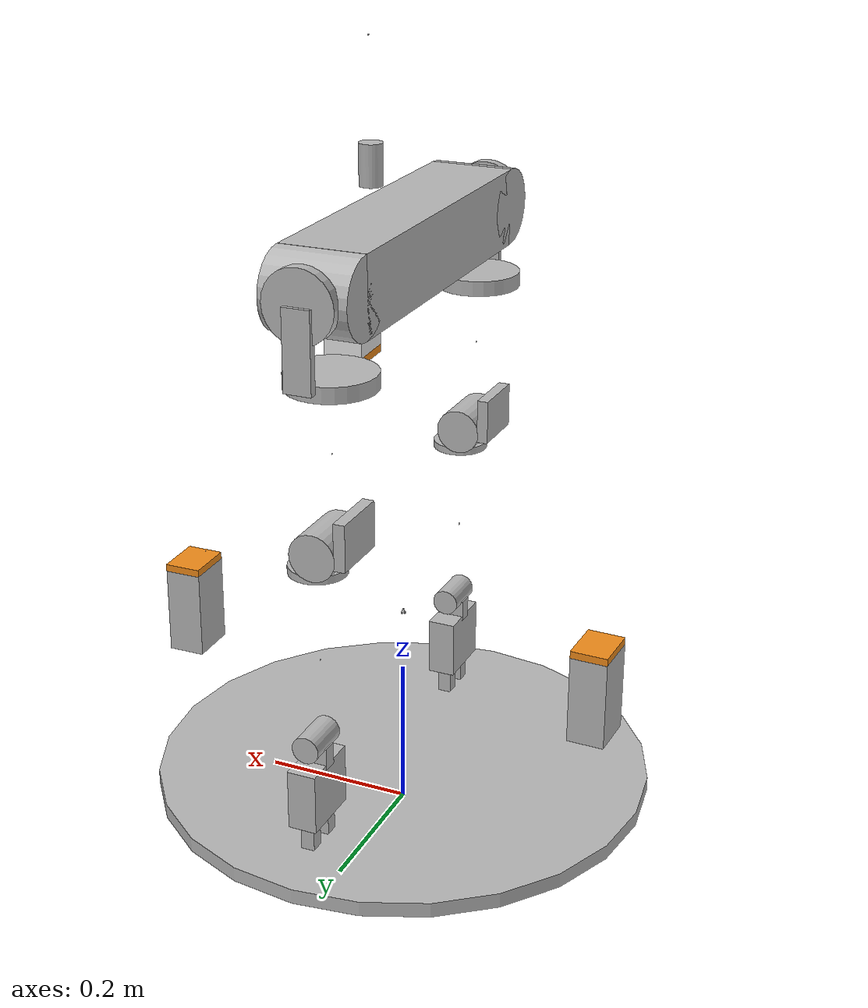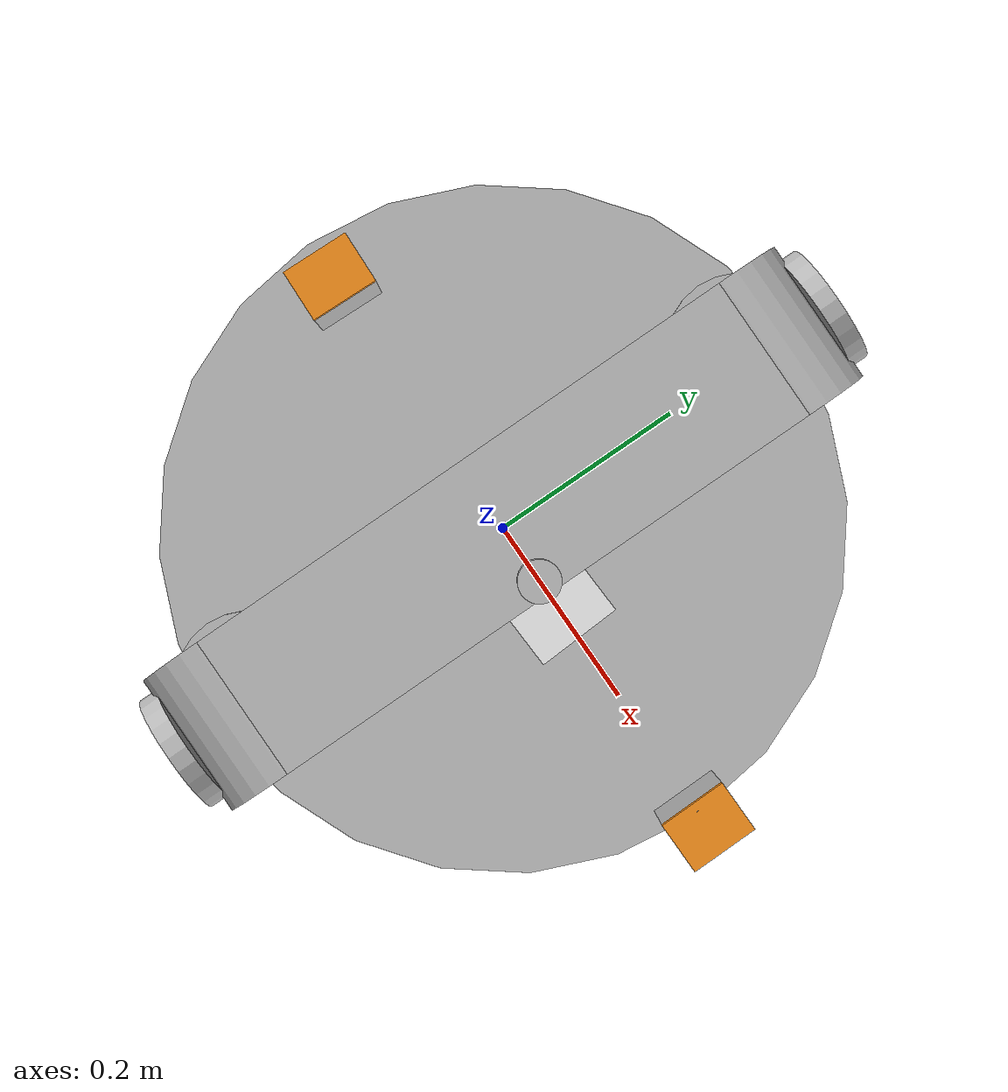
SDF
<sdf version='1.4'>
  <model name='amigo'>
    <link name='amigo/base_link'>
      <pose>0 0 0 0 -0 0</pose>
      <inertial>
        <pose>0.0016583 8.88763e-06 0.376474 0 -0 0</pose>
        <mass>21.153</mass>
        <inertia>
          <ixx>2.66154</ixx>
          <ixy>-5.60882e-05</ixy>
          <ixz>0.00201868</ixz>
          <iyy>2.75667</iyy>
          <iyz>1.1557e-05</iyz>
          <izz>2.50794</izz>
        </inertia>
      </inertial>
      <collision name='amigo/base_link_collision'>
        <pose>0 0 0 0 -0 0</pose>
        <geometry>
          <cylinder>
            <length>0</length>
            <radius>0</radius>
          </cylinder>
        </geometry>
      </collision>
      <collision name='amigo/base_link_collision_amigo/back_laser'>
        <pose>-0.270002 -0.000157937 0.225 0 -0 3.11</pose>
        <geometry>
          <box>
            <size>0.05 0.065 0.12</size>
          </box>
        </geometry>
      </collision>
      <collision name='amigo/base_link_collision_amigo/back_lasertop'>
        <pose>-0.270002 -0.000157937 0.29 0 -0 3.11</pose>
        <geometry>
          <box>
            <size>0.05 0.065 0.01</size>
          </box>
        </geometry>
      </collision>
      <collision name='amigo/base_link_collision_amigo/base'>
        <pose>0 0 0.285 0 0 -1.5708</pose>
        <geometry>
          <mesh>
            <scale>0.0004 0.0004 0.0004</scale>
            <uri>model://media/meshes/bottomcovers.dae</uri>
          </mesh>
        </geometry>
      </collision>
      <collision name='amigo/base_link_collision_amigo/base_kinect/openni_camera'>
        <pose>0.3 0 0.315 0 -0.07 0</pose>
        <geometry>
          <mesh>
            <scale>1 1 1</scale>
            <uri>model://media/meshes/kinect/kinect_without_base.dae</uri>
          </mesh>
        </geometry>
      </collision>
      <collision name='amigo/base_link_collision_amigo/base_laser'>
        <pose>0.318901 -7.49972e-05 0.23 0 -0 0.015</pose>
        <geometry>
          <box>
            <size>0.05 0.065 0.12</size>
          </box>
        </geometry>
      </collision>
      <collision name='amigo/base_link_collision_amigo/base_plate'>
        <pose>0 0 0.05 0 -0 0</pose>
        <geometry>
          <cylinder>
            <length>0.02</length>
            <radius>0.333</radius>
          </cylinder>
        </geometry>
      </collision>
      <collision name='amigo/base_link_collision_amigo/lasertop'>
        <pose>0.318901 -7.49972e-05 0.295 0 -0 0.015</pose>
        <geometry>
          <box>
            <size>0.05 0.065 0.01</size>
          </box>
        </geometry>
      </collision>
      <collision name='amigo/base_link_collision_amigo/logo'>
        <pose>0.348897 0.000374986 0.155 0 -0 -3.12669</pose>
        <geometry>
          <mesh>
            <scale>0.0016 0.0016 0.0016</scale>
            <uri>model://media/meshes/logo.dae</uri>
          </mesh>
        </geometry>
      </collision>
      <visual name='amigo/base_link_visual'>
        <pose>0 0 0 0 -0 0</pose>
        <geometry>
          <cylinder>
            <length>0</length>
            <radius>0</radius>
          </cylinder>
        </geometry>
        <material>
          <script>
            <name>amigo_description/bottomcovers</name>
            <uri>model://media/materials/scripts/tue_mats.material</uri>
          </script>
        </material>
      </visual>
      <visual name='amigo/base_link_visual_amigo/back_laser'>
        <pose>-0.270002 -0.000157937 0.225 0 -0 3.11</pose>
        <geometry>
          <box>
            <size>0.05 0.065 0.12</size>
          </box>
        </geometry>
      </visual>
      <visual name='amigo/base_link_visual_amigo/back_lasertop'>
        <pose>-0.270002 -0.000157937 0.29 0 -0 3.11</pose>
        <geometry>
          <box>
            <size>0.05 0.065 0.01</size>
          </box>
        </geometry>
        <material>
          <script>
            <name>amigo_description/orange</name>
            <uri>model://media/materials/scripts/tue_mats.material</uri>
          </script>
        </material>
        <material>
          <script>
            <name>amigo_description/orange</name>
            <uri>model://media/materials/scripts/tue_mats.material</uri>
          </script>
        </material>
      </visual>
      <visual name='amigo/base_link_visual_amigo/base'>
        <pose>0 0 0.285 0 0 -1.5708</pose>
        <geometry>
          <mesh>
            <scale>0.0004 0.0004 0.0004</scale>
            <uri>model://media/meshes/bottomcovers.dae</uri>
          </mesh>
        </geometry>
        <material>
          <script>
            <name>amigo_description/bottomcovers</name>
            <uri>model://media/materials/scripts/tue_mats.material</uri>
          </script>
        </material>
      </visual>
      <visual name='amigo/base_link_visual_amigo/base_kinect/openni_camera'>
        <pose>0.3 0 0.315 0 -0.07 0</pose>
        <geometry>
          <mesh>
            <scale>1 1 1</scale>
            <uri>model://media/meshes/kinect/kinect_without_base.dae</uri>
          </mesh>
        </geometry>
        <material>
          <script>
            <name>amigo_description/bottomcovers</name>
            <uri>model://media/materials/scripts/tue_mats.material</uri>
          </script>
        </material>
      </visual>
      <visual name='amigo/base_link_visual_amigo/base_laser'>
        <pose>0.318901 -7.49972e-05 0.23 0 -0 0.015</pose>
        <geometry>
          <box>
            <size>0.05 0.065 0.12</size>
          </box>
        </geometry>
        <material>
          <script>
            <name>amigo_description/bottomcovers</name>
            <uri>model://media/materials/scripts/tue_mats.material</uri>
          </script>
        </material>
      </visual>
      <visual name='amigo/base_link_visual_amigo/base_plate'>
        <pose>0 0 0.05 0 -0 0</pose>
        <geometry>
          <cylinder>
            <length>0.02</length>
            <radius>0.333</radius>
          </cylinder>
        </geometry>
        <material>
          <script>
            <name>amigo_description/bottomcovers</name>
            <uri>model://media/materials/scripts/tue_mats.material</uri>
          </script>
        </material>
        <material>
          <script>
            <name>amigo_description/aluminium</name>
            <uri>model://media/materials/scripts/tue_mats.material</uri>
          </script>
        </material>
      </visual>
      <visual name='amigo/base_link_visual_amigo/lasertop'>
        <pose>0.318901 -7.49972e-05 0.295 0 -0 0.015</pose>
        <geometry>
          <box>
            <size>0.05 0.065 0.01</size>
          </box>
        </geometry>
        <material>
          <script>
            <name>amigo_description/orange</name>
            <uri>model://media/materials/scripts/tue_mats.material</uri>
          </script>
        </material>
      </visual>
      <visual name='amigo/base_link_visual_amigo/logo'>
        <pose>0.348897 0.000374986 0.155 0 -0 -3.12669</pose>
        <geometry>
          <mesh>
            <scale>0.0016 0.0016 0.0016</scale>
            <uri>model://media/meshes/logo.dae</uri>
          </mesh>
        </geometry>
        <material>
          <script>
            <name>amigo_description/logo</name>
            <uri>model://media/materials/scripts/tue_mats.material</uri>
          </script>
        </material>
      </visual>
      <velocity_decay>
        <linear>0</linear>
        <angular>0</angular>
      </velocity_decay>
    </link>
    <link name='amigo/torso_slider'>
      <pose>0 0 0.635 -3.58979e-09 -1.57079 3.14159</pose>
      <inertial>
        <pose>0.0968094 0 0.00220002 0 -0 0</pose>
        <mass>16.951</mass>
        <inertia>
          <ixx>0.0979085</ixx>
          <ixy>0</ixy>
          <ixz>0.00337838</ixz>
          <iyy>0.092542</iyy>
          <iyz>1.69407e-21</iyz>
          <izz>0.104374</izz>
        </inertia>
      </inertial>
      <collision name='amigo/torso_slider_collision'>
        <pose>0.05 0 0 0 -0 1.5708</pose>
        <geometry>
          <mesh>
            <scale>0.004 0.004 0.004</scale>
            <uri>model://media/meshes/torsoslidertextured.dae</uri>
          </mesh>
        </geometry>
      </collision>
      <collision name='amigo/torso_slider_collision_amigo/clavicles'>
        <pose>0.15 0 0 0 -0 0</pose>
        <geometry>
          <box>
            <size>0.1 0.436 0.11</size>
          </box>
        </geometry>
      </collision>
      <collision name='amigo/torso_slider_collision_amigo/shoulder_mount_left'>
        <pose>0.15 -0.22 0 0 -0 0</pose>
        <geometry>
          <cylinder>
            <length>0.11</length>
            <radius>0.05</radius>
          </cylinder>
        </geometry>
      </collision>
      <collision name='amigo/torso_slider_collision_amigo/shoulder_mount_right'>
        <pose>0.15 0.22 0 0 -0 0</pose>
        <geometry>
          <cylinder>
            <length>0.11</length>
            <radius>0.05</radius>
          </cylinder>
        </geometry>
      </collision>
      <collision name='amigo/torso_slider_collision_amigo/torso'>
        <pose>0.145 0 0.06 -1.5708 -5.55112e-17 -1.5708</pose>
        <geometry>
          <mesh>
            <scale>0.0004 0.0004 0.0004</scale>
            <uri>model://media/meshes/torsocovers.dae</uri>
          </mesh>
        </geometry>
      </collision>
      <collision name='amigo/torso_slider_collision_amigo/torso_assist_slider_back'>
        <pose>-0.6 0 -0.1 1.5708 -3.67321e-06 1.5708</pose>
        <geometry>
          <mesh>
            <scale>0.004 0.004 0.005</scale>
            <uri>model://media/meshes/torsoassistslidertextured.dae</uri>
          </mesh>
        </geometry>
      </collision>
      <collision name='amigo/torso_slider_collision_amigo/torso_assist_slider_left'>
        <pose>-0.6 -0.1 0 3.14159 1.57079 3.14159</pose>
        <geometry>
          <mesh>
            <scale>0.004 0.004 0.005</scale>
            <uri>model://media/meshes/torsoassistslidertextured.dae</uri>
          </mesh>
        </geometry>
      </collision>
      <collision name='amigo/torso_slider_collision_amigo/torso_assist_slider_right'>
        <pose>-0.6 0.1 0 3.14159 1.57079 3.14159</pose>
        <geometry>
          <mesh>
            <scale>0.004 0.004 0.005</scale>
            <uri>model://media/meshes/torsoassistslidertextured.dae</uri>
          </mesh>
        </geometry>
      </collision>
      <collision name='amigo/torso_slider_collision_amigo/torso_dummy'>
        <pose>0.0006 0 0.075 0 -1.57 0</pose>
        <geometry>
          <cylinder>
            <length>0</length>
            <radius>0</radius>
          </cylinder>
        </geometry>
      </collision>
      <collision name='amigo/torso_slider_collision_amigo/torso_laser'>
        <pose>0.065596 0.000249896 0.0699545 1.55486 -1.52079 -1.55488</pose>
        <geometry>
          <box>
            <size>0.05 0.065 0.12</size>
          </box>
        </geometry>
      </collision>
      <collision name='amigo/torso_slider_collision_amigo/torso_lasertop'>
        <pose>0.000596023 0.000249896 0.0700063 1.55486 -1.52079 -1.55488</pose>
        <geometry>
          <box>
            <size>0.05 0.065 0.01</size>
          </box>
        </geometry>
      </collision>
      <visual name='amigo/torso_slider_visual'>
        <pose>0.05 0 0 0 -0 1.5708</pose>
        <geometry>
          <mesh>
            <scale>0.004 0.004 0.004</scale>
            <uri>model://media/meshes/torsoslidertextured.dae</uri>
          </mesh>
        </geometry>
        <material>
          <script>
            <name>amigo_description/white</name>
            <uri>model://media/materials/scripts/tue_mats.material</uri>
          </script>
        </material>
        <material>
          <script>
            <name>amigo_description/aluminium</name>
            <uri>model://media/materials/scripts/tue_mats.material</uri>
          </script>
        </material>
      </visual>
      <visual name='amigo/torso_slider_visual_amigo/clavicles'>
        <pose>0.15 0 0 0 -0 0</pose>
        <geometry>
          <box>
            <size>0.1 0.436 0.11</size>
          </box>
        </geometry>
      </visual>
      <visual name='amigo/torso_slider_visual_amigo/shoulder_mount_left'>
        <pose>0.15 -0.22 0 0 -0 0</pose>
        <geometry>
          <cylinder>
            <length>0.11</length>
            <radius>0.05</radius>
          </cylinder>
        </geometry>
      </visual>
      <visual name='amigo/torso_slider_visual_amigo/shoulder_mount_right'>
        <pose>0.15 0.22 0 0 -0 0</pose>
        <geometry>
          <cylinder>
            <length>0.11</length>
            <radius>0.05</radius>
          </cylinder>
        </geometry>
      </visual>
      <visual name='amigo/torso_slider_visual_amigo/torso'>
        <pose>0.145 0 0.06 -1.5708 -5.55112e-17 -1.5708</pose>
        <geometry>
          <mesh>
            <scale>0.0004 0.0004 0.0004</scale>
            <uri>model://media/meshes/torsocovers.dae</uri>
          </mesh>
        </geometry>
        <material>
          <script>
            <name>amigo_description/white</name>
            <uri>model://media/materials/scripts/tue_mats.material</uri>
          </script>
        </material>
      </visual>
      <visual name='amigo/torso_slider_visual_amigo/torso_assist_slider_back'>
        <pose>-0.6 0 -0.1 1.5708 -3.67321e-06 1.5708</pose>
        <geometry>
          <mesh>
            <scale>0.004 0.004 0.005</scale>
            <uri>model://media/meshes/torsoassistslidertextured.dae</uri>
          </mesh>
        </geometry>
        <material>
          <script>
            <name>amigo_description/white</name>
            <uri>model://media/materials/scripts/tue_mats.material</uri>
          </script>
        </material>
        <material>
          <script>
            <name>amigo_description/aluminium</name>
            <uri>model://media/materials/scripts/tue_mats.material</uri>
          </script>
        </material>
      </visual>
      <visual name='amigo/torso_slider_visual_amigo/torso_assist_slider_left'>
        <pose>-0.6 -0.1 0 3.14159 1.57079 3.14159</pose>
        <geometry>
          <mesh>
            <scale>0.004 0.004 0.005</scale>
            <uri>model://media/meshes/torsoassistslidertextured.dae</uri>
          </mesh>
        </geometry>
        <material>
          <script>
            <name>amigo_description/white</name>
            <uri>model://media/materials/scripts/tue_mats.material</uri>
          </script>
        </material>
        <material>
          <script>
            <name>amigo_description/aluminium</name>
            <uri>model://media/materials/scripts/tue_mats.material</uri>
          </script>
        </material>
      </visual>
      <visual name='amigo/torso_slider_visual_amigo/torso_assist_slider_right'>
        <pose>-0.6 0.1 0 3.14159 1.57079 3.14159</pose>
        <geometry>
          <mesh>
            <scale>0.004 0.004 0.005</scale>
            <uri>model://media/meshes/torsoassistslidertextured.dae</uri>
          </mesh>
        </geometry>
        <material>
          <script>
            <name>amigo_description/white</name>
            <uri>model://media/materials/scripts/tue_mats.material</uri>
          </script>
        </material>
        <material>
          <script>
            <name>amigo_description/aluminium</name>
            <uri>model://media/materials/scripts/tue_mats.material</uri>
          </script>
        </material>
      </visual>
      <visual name='amigo/torso_slider_visual_amigo/torso_dummy'>
        <pose>0.0006 0 0.075 0 -1.57 0</pose>
        <geometry>
          <cylinder>
            <length>0</length>
            <radius>0</radius>
          </cylinder>
        </geometry>
        <material>
          <script>
            <name>amigo_description/white</name>
            <uri>model://media/materials/scripts/tue_mats.material</uri>
          </script>
        </material>
      </visual>
      <visual name='amigo/torso_slider_visual_amigo/torso_laser'>
        <pose>0.065596 0.000249896 0.0699545 1.55486 -1.52079 -1.55488</pose>
        <geometry>
          <box>
            <size>0.05 0.065 0.12</size>
          </box>
        </geometry>
        <material>
          <script>
            <name>amigo_description/white</name>
            <uri>model://media/materials/scripts/tue_mats.material</uri>
          </script>
        </material>
      </visual>
      <visual name='amigo/torso_slider_visual_amigo/torso_lasertop'>
        <pose>0.000596023 0.000249896 0.0700063 1.55486 -1.52079 -1.55488</pose>
        <geometry>
          <box>
            <size>0.05 0.065 0.01</size>
          </box>
        </geometry>
        <material>
          <script>
            <name>amigo_description/orange</name>
            <uri>model://media/materials/scripts/tue_mats.material</uri>
          </script>
        </material>
        <material>
          <script>
            <name>amigo_description/white</name>
            <uri>model://media/materials/scripts/tue_mats.material</uri>
          </script>
        </material>
        <material>
          <script>
            <name>amigo_description/orange</name>
            <uri>model://media/materials/scripts/tue_mats.material</uri>
          </script>
        </material>
      </visual>
      <velocity_decay>
        <linear>0</linear>
        <angular>0</angular>
      </velocity_decay>
    </link>
    <joint name='torso_joint' type='prismatic'>
      <child>amigo/torso_slider</child>
      <parent>amigo/base_link</parent>
      <axis>
        <xyz>-3.67321e-06 2.06795e-25 1</xyz>
        <limit>
          <lower>0.09</lower>
          <upper>0.4</upper>
          <effort>0.1</effort>
          <velocity>0.07</velocity>
        </limit>
        <dynamics>
          <damping>3</damping>
        </dynamics>
      </axis>
    </joint>
    <link name='amigo/neck_pan'>
      <pose>0.0425992 -1.52925e-10 0.845 -9.26536e-05 1.18826e-16 -3.58979e-09</pose>
      <inertial>
        <pose>0 0 0.0335 0 -0 0</pose>
        <mass>0.05</mass>
        <inertia>
          <ixx>0.0001</ixx>
          <ixy>0</ixy>
          <ixz>0</ixz>
          <iyy>0.0001</iyy>
          <iyz>0</iyz>
          <izz>0.0001</izz>
        </inertia>
      </inertial>
      <collision name='amigo/neck_pan_collision'>
        <pose>0 0 0.0335 0 -0 0</pose>
        <geometry>
          <cylinder>
            <length>0.0525</length>
            <radius>0.015</radius>
          </cylinder>
        </geometry>
      </collision>
      <visual name='amigo/neck_pan_visual'>
        <pose>0 0 0.0335 0 -0 0</pose>
        <geometry>
          <cylinder>
            <length>0.0525</length>
            <radius>0.015</radius>
          </cylinder>
        </geometry>
      </visual>
      <velocity_decay>
        <linear>0</linear>
        <angular>0</angular>
      </velocity_decay>
    </link>
    <joint name='neck_pan_joint' type='revolute'>
      <child>amigo/neck_pan</child>
      <parent>amigo/torso_slider</parent>
      <axis>
        <xyz>3.32726e-13 9.26536e-05 1</xyz>
        <limit>
          <lower>-1.5708</lower>
          <upper>1.5708</upper>
          <effort>13.4</effort>
          <velocity>1</velocity>
        </limit>
        <dynamics>
          <damping>0.1</damping>
        </dynamics>
      </axis>
    </joint>
    <link name='amigo/neck_tilt'>
      <pose>0.0425992 4.12293e-06 0.8895 -9.2664e-05 0.015 -1.3935e-06</pose>
      <inertial>
        <pose>0.0109889 0.00154061 0.0510274 0 -0 0</pose>
        <mass>0.073</mass>
        <inertia>
          <ixx>0.00338239</ixx>
          <ixy>-2.64965e-06</ixy>
          <ixz>-3.92852e-05</ixz>
          <iyy>0.0033997</iyy>
          <iyz>-5.5077e-06</iyz>
          <izz>0.00332102</izz>
        </inertia>
      </inertial>
      <collision name='amigo/neck_tilt_collision'>
        <pose>0 -0 0.015 0 -0 0</pose>
        <geometry>
          <mesh>
            <scale>0.004 0.004 0.004</scale>
            <uri>model://media/meshes/necktilttextured.dae</uri>
          </mesh>
        </geometry>
      </collision>
      <collision name='amigo/neck_tilt_collision_amigo/head'>
        <pose>0 0 0.141 0 0 -1.5708</pose>
        <geometry>
          <mesh>
            <scale>0.0004 0.0004 0.0004</scale>
            <uri>model://media/meshes/headtextured.dae</uri>
          </mesh>
        </geometry>
      </collision>
      <visual name='amigo/neck_tilt_visual'>
        <pose>0 -0 0.015 0 -0 0</pose>
        <geometry>
          <mesh>
            <scale>0.004 0.004 0.004</scale>
            <uri>model://media/meshes/necktilttextured.dae</uri>
          </mesh>
        </geometry>
        <material>
          <script>
            <name>amigo_description/aluminium</name>
            <uri>model://media/materials/scripts/tue_mats.material</uri>
          </script>
        </material>
      </visual>
      <visual name='amigo/neck_tilt_visual_amigo/head'>
        <pose>0 0 0.141 0 0 -1.5708</pose>
        <geometry>
          <mesh>
            <scale>0.0004 0.0004 0.0004</scale>
            <uri>model://media/meshes/headtextured.dae</uri>
          </mesh>
        </geometry>
        <material>
          <script>
            <name>amigo_description/white</name>
            <uri>model://media/materials/scripts/tue_mats.material</uri>
          </script>
        </material>
      </visual>
      <visual name='amigo/neck_tilt_visual_amigo/top_kinect/openni_camera'>
        <pose>0.035 0 0.1 0 -0 0.025</pose>
        <geometry>
          <box>
            <size>0 0 0</size>
          </box>
        </geometry>
      </visual>
      <velocity_decay>
        <linear>0</linear>
        <angular>0</angular>
      </velocity_decay>
    </link>
    <joint name='neck_tilt_joint' type='revolute'>
      <child>amigo/neck_tilt</child>
      <parent>amigo/neck_pan</parent>
      <axis>
        <xyz>3.58979e-09 1 -9.26536e-05</xyz>
        <limit>
          <lower>-0.5</lower>
          <upper>0.88</upper>
          <effort>13.4</effort>
          <velocity>1</velocity>
        </limit>
        <dynamics>
          <damping>0.1</damping>
        </dynamics>
      </axis>
    </joint>
    <link name='amigo/shoulder_link1_left'>
      <pose>-5.50191e-07 0.22 0.785 1.57079 1.36511e-18 -3.58979e-09</pose>
      <inertial>
        <pose>0 0 0 0 -0 0</pose>
        <mass>0.25</mass>
        <inertia>
          <ixx>6</ixx>
          <ixy>0</ixy>
          <ixz>0</ixz>
          <iyy>0.01</iyy>
          <iyz>0</iyz>
          <izz>0.01</izz>
        </inertia>
      </inertial>
      <collision name='amigo/shoulder_link1_left_collision'>
        <pose>0 0 -0.0525 0 -0 0</pose>
        <geometry>
          <cylinder>
            <length>0.015</length>
            <radius>0.045</radius>
          </cylinder>
        </geometry>
      </collision>
      <visual name='amigo/shoulder_link1_left_visual'>
        <pose>0 0 -0.0525 0 -0 0</pose>
        <geometry>
          <cylinder>
            <length>0.015</length>
            <radius>0.045</radius>
          </cylinder>
        </geometry>
      </visual>
      <velocity_decay>
        <linear>0</linear>
        <angular>0</angular>
      </velocity_decay>
    </link>
    <joint name='shoulder_yaw_joint_left' type='revolute'>
      <child>amigo/shoulder_link1_left</child>
      <parent>amigo/torso_slider</parent>
      <axis>
        <xyz>-1 3.58979e-09 1.36511e-18</xyz>
        <limit>
          <lower>-1.57</lower>
          <upper>0</upper>
          <effort>0.2</effort>
          <velocity>0.4</velocity>
        </limit>
        <dynamics>
          <damping>4</damping>
        </dynamics>
      </axis>
    </joint>
    <link name='amigo/shoulder_link2_left'>
      <pose>-5.50191e-07 0.22 0.785 -7.34641e-06 1.36511e-18 -3.58979e-09</pose>
      <inertial>
        <pose>0 0 0 0 -0 0</pose>
        <mass>0.15</mass>
        <inertia>
          <ixx>0.01</ixx>
          <ixy>0</ixy>
          <ixz>0</ixz>
          <iyy>4.04</iyy>
          <iyz>0</iyz>
          <izz>0.001</izz>
        </inertia>
      </inertial>
      <collision name='amigo/shoulder_link2_left_collision'>
        <pose>0 0.06 -0.05 0 -0 0</pose>
        <geometry>
          <box>
            <size>0.035 0.01 0.1</size>
          </box>
        </geometry>
      </collision>
      <visual name='amigo/shoulder_link2_left_visual'>
        <pose>0 0.06 -0.05 0 -0 0</pose>
        <geometry>
          <box>
            <size>0.035 0.01 0.1</size>
          </box>
        </geometry>
      </visual>
      <velocity_decay>
        <linear>0</linear>
        <angular>0</angular>
      </velocity_decay>
    </link>
    <joint name='shoulder_pitch_joint_left' type='revolute'>
      <child>amigo/shoulder_link2_left</child>
      <parent>amigo/shoulder_link1_left</parent>
      <axis>
        <xyz>-3.58979e-09 -1 7.34641e-06</xyz>
        <limit>
          <lower>-1.57</lower>
          <upper>1.57</upper>
          <effort>0.2</effort>
          <velocity>0.4</velocity>
        </limit>
        <dynamics>
          <damping>4</damping>
        </dynamics>
      </axis>
    </joint>
    <link name='amigo/upper_arm_left'>
      <pose>-5.50191e-07 0.22 0.785 1.57079 1.36511e-18 -3.58979e-09</pose>
      <inertial>
        <pose>-3.3557e-05 -0.200403 0 0 -0 0</pose>
        <mass>2.98</mass>
        <inertia>
          <ixx>0.0563415</ixx>
          <ixy>1.00403e-05</ixy>
          <ixz>0</ixz>
          <iyy>0.465931</iyy>
          <iyz>-8.44837e-08</iyz>
          <izz>0.0333425</izz>
        </inertia>
      </inertial>
      <collision name='amigo/upper_arm_left_collision'>
        <pose>-0.00959 -0.19131 -1e-05 0 -0 3.1415</pose>
        <geometry>
          <mesh>
            <scale>0.0004 0.0004 0.0004</scale>
            <uri>model://media/meshes/upperarmtextured.dae</uri>
          </mesh>
        </geometry>
      </collision>
      <collision name='amigo/upper_arm_left_collision_amigo/elbow_extra_block2_left'>
        <pose>0 -0.31 0 0 -0 0</pose>
        <geometry>
          <cylinder>
            <length>0.08</length>
            <radius>0.03</radius>
          </cylinder>
        </geometry>
      </collision>
      <collision name='amigo/upper_arm_left_collision_amigo/elbow_extra_block_left'>
        <pose>-0.036 -0.29 -7.34641e-08 -1.5708 0 0</pose>
        <geometry>
          <box>
            <size>0.015 0.08 0.06</size>
          </box>
        </geometry>
      </collision>
      <collision name='amigo/upper_arm_left_collision_amigo/upper_arm_top_left'>
        <pose>-0.01 -0.1 0 1.5708 -0 0</pose>
        <geometry>
          <cylinder>
            <length>0.02</length>
            <radius>0.0561</radius>
          </cylinder>
        </geometry>
      </collision>
      <visual name='amigo/upper_arm_left_visual'>
        <pose>-0.00959 -0.19131 -1e-05 0 -0 3.1415</pose>
        <geometry>
          <mesh>
            <scale>0.0004 0.0004 0.0004</scale>
            <uri>model://media/meshes/upperarmtextured.dae</uri>
          </mesh>
        </geometry>
        <material>
          <script>
            <name>amigo_description/white</name>
            <uri>model://media/materials/scripts/tue_mats.material</uri>
          </script>
        </material>
      </visual>
      <visual name='amigo/upper_arm_left_visual_amigo/elbow_extra_block2_left'>
        <pose>0 -0.31 0 0 -0 0</pose>
        <geometry>
          <cylinder>
            <length>0.08</length>
            <radius>0.03</radius>
          </cylinder>
        </geometry>
      </visual>
      <visual name='amigo/upper_arm_left_visual_amigo/elbow_extra_block_left'>
        <pose>-0.036 -0.29 -7.34641e-08 -1.5708 0 0</pose>
        <geometry>
          <box>
            <size>0.015 0.08 0.06</size>
          </box>
        </geometry>
      </visual>
      <visual name='amigo/upper_arm_left_visual_amigo/upper_arm_top_left'>
        <pose>-0.01 -0.1 0 1.5708 -0 0</pose>
        <geometry>
          <cylinder>
            <length>0.02</length>
            <radius>0.0561</radius>
          </cylinder>
        </geometry>
      </visual>
      <velocity_decay>
        <linear>0</linear>
        <angular>0</angular>
      </velocity_decay>
    </link>
    <joint name='shoulder_roll_joint_left' type='revolute'>
      <child>amigo/upper_arm_left</child>
      <parent>amigo/shoulder_link2_left</parent>
      <axis>
        <xyz>-1.31874e-14 -3.67321e-06 -1</xyz>
        <limit>
          <lower>-1.57</lower>
          <upper>1.57</upper>
          <effort>0.3</effort>
          <velocity>0.6</velocity>
        </limit>
        <dynamics>
          <damping>3.8</damping>
        </dynamics>
      </axis>
    </joint>
    <link name='amigo/elbow_link4_left'>
      <pose>0.00999945 0.219999 0.465 -7.34641e-06 1.36511e-18 -3.58979e-09</pose>
      <inertial>
        <pose>0 0 0 0 -0 0</pose>
        <mass>0.1</mass>
        <inertia>
          <ixx>0.001</ixx>
          <ixy>0</ixy>
          <ixz>0</ixz>
          <iyy>0.6</iyy>
          <iyz>0</iyz>
          <izz>0.001</izz>
        </inertia>
      </inertial>
      <collision name='amigo/elbow_link4_left_collision'>
        <pose>0 0 0 0 -0 0</pose>
        <geometry>
          <cylinder>
            <length>0</length>
            <radius>0</radius>
          </cylinder>
        </geometry>
      </collision>
      <visual name='amigo/elbow_link4_left_visual'>
        <pose>0 0 0 0 -0 0</pose>
        <geometry>
          <cylinder>
            <length>0</length>
            <radius>0</radius>
          </cylinder>
        </geometry>
      </visual>
      <velocity_decay>
        <linear>0</linear>
        <angular>0</angular>
      </velocity_decay>
    </link>
    <joint name='elbow_pitch_joint_left' type='revolute'>
      <child>amigo/elbow_link4_left</child>
      <parent>amigo/upper_arm_left</parent>
      <axis>
        <xyz>-3.58979e-09 -1 7.34641e-06</xyz>
        <limit>
          <lower>0</lower>
          <upper>2.23</upper>
          <effort>0.5</effort>
          <velocity>0.8</velocity>
        </limit>
        <dynamics>
          <damping>3</damping>
        </dynamics>
      </axis>
    </joint>
    <link name='amigo/fore_arm_left'>
      <pose>0.00999945 0.219999 0.465 1.57079 1.36511e-18 -3.58979e-09</pose>
      <inertial>
        <pose>2.32558e-05 -0.1385 0 0 -0 0</pose>
        <mass>0.86</mass>
        <inertia>
          <ixx>0.00656447</ixx>
          <ixy>-2.55e-06</ixy>
          <ixz>0</ixz>
          <iyy>0.5004</iyy>
          <iyz>-1.8366e-08</iyz>
          <izz>0.00656451</izz>
        </inertia>
      </inertial>
      <collision name='amigo/fore_arm_left_collision'>
        <pose>0.00425 -0.14868 0.00547 3.14159 -1.57079 3.14159</pose>
        <geometry>
          <mesh>
            <scale>0.0004 0.0004 0.0004</scale>
            <uri>model://media/meshes/forearmtextured.dae</uri>
          </mesh>
        </geometry>
      </collision>
      <collision name='amigo/fore_arm_left_collision_amigo/fore_arm_top_left'>
        <pose>0.002 -0.021 -3.67321e-08 1.5708 -0 0</pose>
        <geometry>
          <cylinder>
            <length>0.01</length>
            <radius>0.037</radius>
          </cylinder>
        </geometry>
      </collision>
      <visual name='amigo/fore_arm_left_visual'>
        <pose>0.00425 -0.14868 0.00547 3.14159 -1.57079 3.14159</pose>
        <geometry>
          <mesh>
            <scale>0.0004 0.0004 0.0004</scale>
            <uri>model://media/meshes/forearmtextured.dae</uri>
          </mesh>
        </geometry>
        <material>
          <script>
            <name>amigo_description/white</name>
            <uri>model://media/materials/scripts/tue_mats.material</uri>
          </script>
        </material>
      </visual>
      <visual name='amigo/fore_arm_left_visual_amigo/fore_arm_top_left'>
        <pose>0.002 -0.021 -3.67321e-08 1.5708 -0 0</pose>
        <geometry>
          <cylinder>
            <length>0.01</length>
            <radius>0.037</radius>
          </cylinder>
        </geometry>
      </visual>
      <velocity_decay>
        <linear>0</linear>
        <angular>0</angular>
      </velocity_decay>
    </link>
    <joint name='elbow_roll_joint_left' type='revolute'>
      <child>amigo/fore_arm_left</child>
      <parent>amigo/elbow_link4_left</parent>
      <axis>
        <xyz>-1.31874e-14 -3.67321e-06 -1</xyz>
        <limit>
          <lower>-1.83</lower>
          <upper>1.83</upper>
          <effort>0.5</effort>
          <velocity>0.8</velocity>
        </limit>
        <dynamics>
          <damping>3.5</damping>
        </dynamics>
      </axis>
    </joint>
    <link name='amigo/wrist_link6_left'>
      <pose>0.0199994 0.219998 0.185 -2.3562 1.57079 -2.35619</pose>
      <inertial>
        <pose>-0.00666667 0 0 0 -0 0</pose>
        <mass>0.03</mass>
        <inertia>
          <ixx>0.003</ixx>
          <ixy>0</ixy>
          <ixz>0</ixz>
          <iyy>0.0352227</iyy>
          <iyz>4.1359e-25</iyz>
          <izz>0.00300267</izz>
        </inertia>
      </inertial>
      <collision name='amigo/wrist_link6_left_collision'>
        <pose>0 0 0 1.5708 -0 0</pose>
        <geometry>
          <cylinder>
            <length>0</length>
            <radius>0</radius>
          </cylinder>
        </geometry>
      </collision>
      <collision name='amigo/wrist_link6_left_collision_amigo/wrist_to_hand_block_left'>
        <pose>0 0 0 0 -0 0</pose>
        <geometry>
          <box>
            <size>0.03 0.02 0.038</size>
          </box>
        </geometry>
      </collision>
      <collision name='amigo/wrist_link6_left_collision_amigo/wrist_visual_left'>
        <pose>-0.02 0 0 1.5708 -0 0</pose>
        <geometry>
          <cylinder>
            <length>0.06</length>
            <radius>0.018</radius>
          </cylinder>
        </geometry>
      </collision>
      <visual name='amigo/wrist_link6_left_visual'>
        <pose>0 0 0 1.5708 -0 0</pose>
        <geometry>
          <cylinder>
            <length>0</length>
            <radius>0</radius>
          </cylinder>
        </geometry>
      </visual>
      <visual name='amigo/wrist_link6_left_visual_amigo/wrist_to_hand_block_left'>
        <pose>0 0 0 0 -0 0</pose>
        <geometry>
          <box>
            <size>0.03 0.02 0.038</size>
          </box>
        </geometry>
      </visual>
      <visual name='amigo/wrist_link6_left_visual_amigo/wrist_visual_left'>
        <pose>-0.02 0 0 1.5708 -0 0</pose>
        <geometry>
          <cylinder>
            <length>0.06</length>
            <radius>0.018</radius>
          </cylinder>
        </geometry>
      </visual>
      <velocity_decay>
        <linear>0</linear>
        <angular>0</angular>
      </velocity_decay>
    </link>
    <joint name='wrist_pitch_joint_left' type='revolute'>
      <child>amigo/wrist_link6_left</child>
      <parent>amigo/fore_arm_left</parent>
      <axis>
        <xyz>3.66962e-06 -1 3.67319e-06</xyz>
        <limit>
          <lower>-0.95</lower>
          <upper>0.95</upper>
          <effort>0.5</effort>
          <velocity>1</velocity>
        </limit>
        <dynamics>
          <damping>0.35</damping>
        </dynamics>
      </axis>
    </joint>
    <link name='amigo/hand_left'>
      <pose>0.0199994 0.219998 0.185 -2.3562 1.57079 -2.35619</pose>
      <inertial>
        <pose>0.047619 0 0 0 -0 0</pose>
        <mass>0.21</mass>
        <inertia>
          <ixx>0.0101</ixx>
          <ixy>0</ixy>
          <ixz>0</ixz>
          <iyy>0.0101006</iyy>
          <iyz>0</iyz>
          <izz>0.0623006</izz>
        </inertia>
      </inertial>
      <collision name='amigo/hand_left_collision'>
        <pose>0.048 0 0 0 -0 0</pose>
        <geometry>
          <box>
            <size>0.08 0.085 0.038</size>
          </box>
        </geometry>
      </collision>
      <collision name='amigo/hand_left_collision_amigo/grippoint_left'>
        <pose>0.04 0 0 0 -0 0</pose>
        <geometry>
          <box>
            <size>0 0 0</size>
          </box>
        </geometry>
      </collision>
      <visual name='amigo/hand_left_visual'>
        <pose>0.048 0 0 0 -0 0</pose>
        <geometry>
          <box>
            <size>0.08 0.085 0.038</size>
          </box>
        </geometry>
      </visual>
      <visual name='amigo/hand_left_visual_amigo/grippoint_left'>
        <pose>0.04 0 0 0 -0 0</pose>
        <geometry>
          <box>
            <size>0 0 0</size>
          </box>
        </geometry>
      </visual>
      <velocity_decay>
        <linear>0</linear>
        <angular>0</angular>
      </velocity_decay>
    </link>
    <joint name='wrist_yaw_joint_left' type='revolute'>
      <child>amigo/hand_left</child>
      <parent>amigo/wrist_link6_left</parent>
      <axis>
        <xyz>-1.01 -3.7063e-06 3.70995e-06</xyz>
        <limit>
          <lower>-0.61</lower>
          <upper>0.61</upper>
          <effort>0.5</effort>
          <velocity>1</velocity>
        </limit>
        <dynamics>
          <damping>0.3</damping>
        </dynamics>
      </axis>
    </joint>
    <link name='amigo/finger1_left'>
      <pose>0.0199991 0.239998 0.11 -3.67319e-06 0.0008 3.66668e-06</pose>
      <inertial>
        <pose>0 0 -0.045 0 -0 0</pose>
        <mass>0.02</mass>
        <inertia>
          <ixx>0.0110045</ixx>
          <ixy>0</ixy>
          <ixz>1.05879e-22</ixz>
          <iyy>0.0110045</iyy>
          <iyz>0</iyz>
          <izz>0.011</izz>
        </inertia>
      </inertial>
      <collision name='amigo/finger1_left_collision'>
        <pose>0 0 -0.03 0 -0 0</pose>
        <geometry>
          <box>
            <size>0.018 0.018 0.06</size>
          </box>
        </geometry>
      </collision>
      <collision name='amigo/finger1_left_collision_amigo/finger1_phalanx_left'>
        <pose>0 0 -0.06 0 1.57 0</pose>
        <geometry>
          <cylinder>
            <length>0.019</length>
            <radius>0.009</radius>
          </cylinder>
        </geometry>
      </collision>
      <visual name='amigo/finger1_left_visual'>
        <pose>0 0 -0.03 0 -0 0</pose>
        <geometry>
          <box>
            <size>0.018 0.018 0.06</size>
          </box>
        </geometry>
      </visual>
      <visual name='amigo/finger1_left_visual_amigo/finger1_phalanx_left'>
        <pose>0 0 -0.06 0 1.57 0</pose>
        <geometry>
          <cylinder>
            <length>0.019</length>
            <radius>0.009</radius>
          </cylinder>
        </geometry>
      </visual>
      <velocity_decay>
        <linear>0</linear>
        <angular>0</angular>
      </velocity_decay>
    </link>
    <joint name='finger1_joint_left' type='revolute'>
      <child>amigo/finger1_left</child>
      <parent>amigo/hand_left</parent>
      <axis>
        <xyz>1 3.66668e-06 -0.0008</xyz>
        <limit>
          <lower>0.2</lower>
          <upper>1</upper>
          <effort>3</effort>
          <velocity>1</velocity>
        </limit>
        <dynamics>
          <damping>0.5</damping>
        </dynamics>
      </axis>
    </joint>
    <link name='amigo/finger1_tip_left'>
      <pose>0.0199511 0.239997 0.0499999 -3.67319e-06 0.0008 3.66668e-06</pose>
      <inertial>
        <pose>0 0 -0.045 0 -0 0</pose>
        <mass>0.02</mass>
        <inertia>
          <ixx>0.0013745</ixx>
          <ixy>0</ixy>
          <ixz>1.05879e-22</ixz>
          <iyy>0.0015245</iyy>
          <iyz>0</iyz>
          <izz>0.00152</izz>
        </inertia>
      </inertial>
      <collision name='amigo/finger1_tip_left_collision'>
        <pose>0 0 -0.03 0 -0 0</pose>
        <geometry>
          <box>
            <size>0.018 0.018 0.06</size>
          </box>
        </geometry>
      </collision>
      <collision name='amigo/finger1_tip_left_collision_amigo/finger1_tip_phalanx_left'>
        <pose>0 0 -0.06 0 1.57 0</pose>
        <geometry>
          <cylinder>
            <length>0.017</length>
            <radius>0.009</radius>
          </cylinder>
        </geometry>
      </collision>
      <visual name='amigo/finger1_tip_left_visual'>
        <pose>0 0 -0.03 0 -0 0</pose>
        <geometry>
          <box>
            <size>0.018 0.018 0.06</size>
          </box>
        </geometry>
      </visual>
      <visual name='amigo/finger1_tip_left_visual_amigo/finger1_tip_phalanx_left'>
        <pose>0 0 -0.06 0 1.57 0</pose>
        <geometry>
          <cylinder>
            <length>0.017</length>
            <radius>0.009</radius>
          </cylinder>
        </geometry>
      </visual>
      <velocity_decay>
        <linear>0</linear>
        <angular>0</angular>
      </velocity_decay>
    </link>
    <joint name='finger1_tip_joint_left' type='revolute'>
      <child>amigo/finger1_tip_left</child>
      <parent>amigo/finger1_left</parent>
      <axis>
        <xyz>1 3.66668e-06 -0.0008</xyz>
        <limit>
          <lower>-0.6</lower>
          <upper>-0.2</upper>
          <effort>3</effort>
          <velocity>1</velocity>
        </limit>
        <dynamics>
          <damping>0.5</damping>
        </dynamics>
      </axis>
    </joint>
    <link name='amigo/finger2_left'>
      <pose>0.0199992 0.199998 0.11 -3.67319e-06 0.0008 3.66668e-06</pose>
      <inertial>
        <pose>0 0 -0.045 0 -0 0</pose>
        <mass>0.02</mass>
        <inertia>
          <ixx>0.0110045</ixx>
          <ixy>0</ixy>
          <ixz>1.05879e-22</ixz>
          <iyy>0.0110045</iyy>
          <iyz>0</iyz>
          <izz>0.011</izz>
        </inertia>
      </inertial>
      <collision name='amigo/finger2_left_collision'>
        <pose>0 0 -0.03 0 -0 0</pose>
        <geometry>
          <box>
            <size>0.018 0.018 0.06</size>
          </box>
        </geometry>
      </collision>
      <collision name='amigo/finger2_left_collision_amigo/finger2_phalanx_left'>
        <pose>0 0 -0.06 0 1.57 0</pose>
        <geometry>
          <cylinder>
            <length>0.019</length>
            <radius>0.009</radius>
          </cylinder>
        </geometry>
      </collision>
      <visual name='amigo/finger2_left_visual'>
        <pose>0 0 -0.03 0 -0 0</pose>
        <geometry>
          <box>
            <size>0.018 0.018 0.06</size>
          </box>
        </geometry>
      </visual>
      <visual name='amigo/finger2_left_visual_amigo/finger2_phalanx_left'>
        <pose>0 0 -0.06 0 1.57 0</pose>
        <geometry>
          <cylinder>
            <length>0.019</length>
            <radius>0.009</radius>
          </cylinder>
        </geometry>
      </visual>
      <velocity_decay>
        <linear>0</linear>
        <angular>0</angular>
      </velocity_decay>
    </link>
    <joint name='finger2_joint_left' type='revolute'>
      <child>amigo/finger2_left</child>
      <parent>amigo/hand_left</parent>
      <axis>
        <xyz>-1 -3.66668e-06 0.0008</xyz>
        <limit>
          <lower>0.2</lower>
          <upper>1</upper>
          <effort>3</effort>
          <velocity>1</velocity>
        </limit>
        <dynamics>
          <damping>0.5</damping>
        </dynamics>
      </axis>
    </joint>
    <link name='amigo/finger2_tip_left'>
      <pose>0.0199512 0.199997 0.0500001 -3.67319e-06 0.0008 3.66668e-06</pose>
      <inertial>
        <pose>0 0 -0.045 0 -0 0</pose>
        <mass>0.02</mass>
        <inertia>
          <ixx>0.0013745</ixx>
          <ixy>0</ixy>
          <ixz>1.05879e-22</ixz>
          <iyy>0.0015245</iyy>
          <iyz>0</iyz>
          <izz>0.00152</izz>
        </inertia>
      </inertial>
      <collision name='amigo/finger2_tip_left_collision'>
        <pose>0 0 -0.03 0 -0 0</pose>
        <geometry>
          <box>
            <size>0.018 0.018 0.06</size>
          </box>
        </geometry>
      </collision>
      <collision name='amigo/finger2_tip_left_collision_amigo/finger2_tip_phalanx_left'>
        <pose>0 0 -0.06 0 1.57 0</pose>
        <geometry>
          <cylinder>
            <length>0.017</length>
            <radius>0.009</radius>
          </cylinder>
        </geometry>
      </collision>
      <visual name='amigo/finger2_tip_left_visual'>
        <pose>0 0 -0.03 0 -0 0</pose>
        <geometry>
          <box>
            <size>0.018 0.018 0.06</size>
          </box>
        </geometry>
      </visual>
      <visual name='amigo/finger2_tip_left_visual_amigo/finger2_tip_phalanx_left'>
        <pose>0 0 -0.06 0 1.57 0</pose>
        <geometry>
          <cylinder>
            <length>0.017</length>
            <radius>0.009</radius>
          </cylinder>
        </geometry>
      </visual>
      <velocity_decay>
        <linear>0</linear>
        <angular>0</angular>
      </velocity_decay>
    </link>
    <joint name='finger2_tip_joint_left' type='revolute'>
      <child>amigo/finger2_tip_left</child>
      <parent>amigo/finger2_left</parent>
      <axis>
        <xyz>-1 -3.66668e-06 0.0008</xyz>
        <limit>
          <lower>-0.6</lower>
          <upper>-0.2</upper>
          <effort>3</effort>
          <velocity>1</velocity>
        </limit>
        <dynamics>
          <damping>0.5</damping>
        </dynamics>
      </axis>
    </joint>
    <link name='amigo/shoulder_link1_right'>
      <pose>-5.51771e-07 -0.22 0.785 1.57079 1.36511e-18 -3.58979e-09</pose>
      <inertial>
        <pose>0 0 0 0 -0 0</pose>
        <mass>0.25</mass>
        <inertia>
          <ixx>6</ixx>
          <ixy>0</ixy>
          <ixz>0</ixz>
          <iyy>0.01</iyy>
          <iyz>0</iyz>
          <izz>0.01</izz>
        </inertia>
      </inertial>
      <collision name='amigo/shoulder_link1_right_collision'>
        <pose>0 0 0.0525 0 -0 0</pose>
        <geometry>
          <cylinder>
            <length>0.015</length>
            <radius>0.045</radius>
          </cylinder>
        </geometry>
      </collision>
      <visual name='amigo/shoulder_link1_right_visual'>
        <pose>0 0 0.0525 0 -0 0</pose>
        <geometry>
          <cylinder>
            <length>0.015</length>
            <radius>0.045</radius>
          </cylinder>
        </geometry>
      </visual>
      <velocity_decay>
        <linear>0</linear>
        <angular>0</angular>
      </velocity_decay>
    </link>
    <joint name='shoulder_yaw_joint_right' type='revolute'>
      <child>amigo/shoulder_link1_right</child>
      <parent>amigo/torso_slider</parent>
      <axis>
        <xyz>1 -3.58979e-09 -1.36511e-18</xyz>
        <limit>
          <lower>-1.57</lower>
          <upper>0</upper>
          <effort>0.2</effort>
          <velocity>0.4</velocity>
        </limit>
        <dynamics>
          <damping>4</damping>
        </dynamics>
      </axis>
    </joint>
    <link name='amigo/shoulder_link2_right'>
      <pose>-5.51771e-07 -0.22 0.785 -7.34641e-06 1.36511e-18 -3.58979e-09</pose>
      <inertial>
        <pose>0 0 0 0 -0 0</pose>
        <mass>0.15</mass>
        <inertia>
          <ixx>0.01</ixx>
          <ixy>0</ixy>
          <ixz>0</ixz>
          <iyy>4.04</iyy>
          <iyz>0</iyz>
          <izz>0.001</izz>
        </inertia>
      </inertial>
      <collision name='amigo/shoulder_link2_right_collision'>
        <pose>0 -0.06 -0.05 0 -0 0</pose>
        <geometry>
          <box>
            <size>0.035 0.01 0.1</size>
          </box>
        </geometry>
      </collision>
      <visual name='amigo/shoulder_link2_right_visual'>
        <pose>0 -0.06 -0.05 0 -0 0</pose>
        <geometry>
          <box>
            <size>0.035 0.01 0.1</size>
          </box>
        </geometry>
      </visual>
      <velocity_decay>
        <linear>0</linear>
        <angular>0</angular>
      </velocity_decay>
    </link>
    <joint name='shoulder_pitch_joint_right' type='revolute'>
      <child>amigo/shoulder_link2_right</child>
      <parent>amigo/shoulder_link1_right</parent>
      <axis>
        <xyz>-3.58979e-09 -1 7.34641e-06</xyz>
        <limit>
          <lower>-1.57</lower>
          <upper>1.57</upper>
          <effort>0.2</effort>
          <velocity>0.4</velocity>
        </limit>
        <dynamics>
          <damping>4</damping>
        </dynamics>
      </axis>
    </joint>
    <link name='amigo/upper_arm_right'>
      <pose>-5.51771e-07 -0.22 0.785 1.57079 1.36511e-18 -3.58979e-09</pose>
      <inertial>
        <pose>-3.3557e-05 -0.200403 0 0 -0 0</pose>
        <mass>2.98</mass>
        <inertia>
          <ixx>0.0563415</ixx>
          <ixy>1.00403e-05</ixy>
          <ixz>0</ixz>
          <iyy>0.465931</iyy>
          <iyz>-8.44837e-08</iyz>
          <izz>0.0333425</izz>
        </inertia>
      </inertial>
      <collision name='amigo/upper_arm_right_collision'>
        <pose>-0.00959 -0.19131 -1e-05 0 -0 3.1415</pose>
        <geometry>
          <mesh>
            <scale>0.0004 0.0004 0.0004</scale>
            <uri>model://media/meshes/upperarmtextured.dae</uri>
          </mesh>
        </geometry>
      </collision>
      <collision name='amigo/upper_arm_right_collision_amigo/elbow_extra_block2_right'>
        <pose>0 -0.31 0 0 -0 0</pose>
        <geometry>
          <cylinder>
            <length>0.08</length>
            <radius>0.03</radius>
          </cylinder>
        </geometry>
      </collision>
      <collision name='amigo/upper_arm_right_collision_amigo/elbow_extra_block_right'>
        <pose>-0.036 -0.29 -7.34641e-08 -1.5708 0 0</pose>
        <geometry>
          <box>
            <size>0.015 0.08 0.06</size>
          </box>
        </geometry>
      </collision>
      <collision name='amigo/upper_arm_right_collision_amigo/upper_arm_top_right'>
        <pose>-0.01 -0.1 0 1.5708 -0 0</pose>
        <geometry>
          <cylinder>
            <length>0.02</length>
            <radius>0.0561</radius>
          </cylinder>
        </geometry>
      </collision>
      <visual name='amigo/upper_arm_right_visual'>
        <pose>-0.00959 -0.19131 -1e-05 0 -0 3.1415</pose>
        <geometry>
          <mesh>
            <scale>0.0004 0.0004 0.0004</scale>
            <uri>model://media/meshes/upperarmtextured.dae</uri>
          </mesh>
        </geometry>
        <material>
          <script>
            <name>amigo_description/white</name>
            <uri>model://media/materials/scripts/tue_mats.material</uri>
          </script>
        </material>
      </visual>
      <visual name='amigo/upper_arm_right_visual_amigo/elbow_extra_block2_right'>
        <pose>0 -0.31 0 0 -0 0</pose>
        <geometry>
          <cylinder>
            <length>0.08</length>
            <radius>0.03</radius>
          </cylinder>
        </geometry>
      </visual>
      <visual name='amigo/upper_arm_right_visual_amigo/elbow_extra_block_right'>
        <pose>-0.036 -0.29 -7.34641e-08 -1.5708 0 0</pose>
        <geometry>
          <box>
            <size>0.015 0.08 0.06</size>
          </box>
        </geometry>
      </visual>
      <visual name='amigo/upper_arm_right_visual_amigo/upper_arm_top_right'>
        <pose>-0.01 -0.1 0 1.5708 -0 0</pose>
        <geometry>
          <cylinder>
            <length>0.02</length>
            <radius>0.0561</radius>
          </cylinder>
        </geometry>
      </visual>
      <velocity_decay>
        <linear>0</linear>
        <angular>0</angular>
      </velocity_decay>
    </link>
    <joint name='shoulder_roll_joint_right' type='revolute'>
      <child>amigo/upper_arm_right</child>
      <parent>amigo/shoulder_link2_right</parent>
      <axis>
        <xyz>1.31874e-14 3.67321e-06 1</xyz>
        <limit>
          <lower>-1.57</lower>
          <upper>1.57</upper>
          <effort>0.3</effort>
          <velocity>0.6</velocity>
        </limit>
        <dynamics>
          <damping>3.8</damping>
        </dynamics>
      </axis>
    </joint>
    <link name='amigo/elbow_link4_right'>
      <pose>0.00999945 -0.220001 0.465 -7.34641e-06 1.36511e-18 -3.58979e-09</pose>
      <inertial>
        <pose>0 0 0 0 -0 0</pose>
        <mass>0.1</mass>
        <inertia>
          <ixx>0.001</ixx>
          <ixy>0</ixy>
          <ixz>0</ixz>
          <iyy>0.6</iyy>
          <iyz>0</iyz>
          <izz>0.001</izz>
        </inertia>
      </inertial>
      <collision name='amigo/elbow_link4_right_collision'>
        <pose>0 0 0 0 -0 0</pose>
        <geometry>
          <cylinder>
            <length>0</length>
            <radius>0</radius>
          </cylinder>
        </geometry>
      </collision>
      <visual name='amigo/elbow_link4_right_visual'>
        <pose>0 0 0 0 -0 0</pose>
        <geometry>
          <cylinder>
            <length>0</length>
            <radius>0</radius>
          </cylinder>
        </geometry>
      </visual>
      <velocity_decay>
        <linear>0</linear>
        <angular>0</angular>
      </velocity_decay>
    </link>
    <joint name='elbow_pitch_joint_right' type='revolute'>
      <child>amigo/elbow_link4_right</child>
      <parent>amigo/upper_arm_right</parent>
      <axis>
        <xyz>-3.58979e-09 -1 7.34641e-06</xyz>
        <limit>
          <lower>0</lower>
          <upper>2.23</upper>
          <effort>0.5</effort>
          <velocity>0.8</velocity>
        </limit>
        <dynamics>
          <damping>3</damping>
        </dynamics>
      </axis>
    </joint>
    <link name='amigo/fore_arm_right'>
      <pose>0.00999945 -0.220001 0.465 1.57079 1.36511e-18 -3.58979e-09</pose>
      <inertial>
        <pose>2.32558e-05 -0.1385 0 0 -0 0</pose>
        <mass>0.86</mass>
        <inertia>
          <ixx>0.00656447</ixx>
          <ixy>-2.55e-06</ixy>
          <ixz>0</ixz>
          <iyy>0.5004</iyy>
          <iyz>-1.8366e-08</iyz>
          <izz>0.00656451</izz>
        </inertia>
      </inertial>
      <collision name='amigo/fore_arm_right_collision'>
        <pose>0.00425 -0.14868 0.00547 3.14159 -1.57079 3.14159</pose>
        <geometry>
          <mesh>
            <scale>0.0004 0.0004 0.0004</scale>
            <uri>model://media/meshes/forearmtextured.dae</uri>
          </mesh>
        </geometry>
      </collision>
      <collision name='amigo/fore_arm_right_collision_amigo/fore_arm_top_right'>
        <pose>0.002 -0.021 -3.67321e-08 1.5708 -0 0</pose>
        <geometry>
          <cylinder>
            <length>0.01</length>
            <radius>0.037</radius>
          </cylinder>
        </geometry>
      </collision>
      <visual name='amigo/fore_arm_right_visual'>
        <pose>0.00425 -0.14868 0.00547 3.14159 -1.57079 3.14159</pose>
        <geometry>
          <mesh>
            <scale>0.0004 0.0004 0.0004</scale>
            <uri>model://media/meshes/forearmtextured.dae</uri>
          </mesh>
        </geometry>
        <material>
          <script>
            <name>amigo_description/white</name>
            <uri>model://media/materials/scripts/tue_mats.material</uri>
          </script>
        </material>
      </visual>
      <visual name='amigo/fore_arm_right_visual_amigo/fore_arm_top_right'>
        <pose>0.002 -0.021 -3.67321e-08 1.5708 -0 0</pose>
        <geometry>
          <cylinder>
            <length>0.01</length>
            <radius>0.037</radius>
          </cylinder>
        </geometry>
      </visual>
      <velocity_decay>
        <linear>0</linear>
        <angular>0</angular>
      </velocity_decay>
    </link>
    <joint name='elbow_roll_joint_right' type='revolute'>
      <child>amigo/fore_arm_right</child>
      <parent>amigo/elbow_link4_right</parent>
      <axis>
        <xyz>1.31874e-14 3.67321e-06 1</xyz>
        <limit>
          <lower>-1.83</lower>
          <upper>1.83</upper>
          <effort>0.5</effort>
          <velocity>0.8</velocity>
        </limit>
        <dynamics>
          <damping>3.5</damping>
        </dynamics>
      </axis>
    </joint>
    <link name='amigo/wrist_link6_right'>
      <pose>0.0199994 -0.220002 0.185 -2.3562 1.57079 -2.35619</pose>
      <inertial>
        <pose>-0.00666667 0 0 0 -0 0</pose>
        <mass>0.03</mass>
        <inertia>
          <ixx>0.003</ixx>
          <ixy>0</ixy>
          <ixz>0</ixz>
          <iyy>0.0352227</iyy>
          <iyz>4.1359e-25</iyz>
          <izz>0.00300267</izz>
        </inertia>
      </inertial>
      <collision name='amigo/wrist_link6_right_collision'>
        <pose>0 0 0 1.5708 -0 0</pose>
        <geometry>
          <cylinder>
            <length>0</length>
            <radius>0</radius>
          </cylinder>
        </geometry>
      </collision>
      <collision name='amigo/wrist_link6_right_collision_amigo/wrist_to_hand_block_right'>
        <pose>0 0 0 0 -0 0</pose>
        <geometry>
          <box>
            <size>0.03 0.02 0.038</size>
          </box>
        </geometry>
      </collision>
      <collision name='amigo/wrist_link6_right_collision_amigo/wrist_visual_right'>
        <pose>-0.02 0 0 1.5708 -0 0</pose>
        <geometry>
          <cylinder>
            <length>0.06</length>
            <radius>0.018</radius>
          </cylinder>
        </geometry>
      </collision>
      <visual name='amigo/wrist_link6_right_visual'>
        <pose>0 0 0 1.5708 -0 0</pose>
        <geometry>
          <cylinder>
            <length>0</length>
            <radius>0</radius>
          </cylinder>
        </geometry>
      </visual>
      <visual name='amigo/wrist_link6_right_visual_amigo/wrist_to_hand_block_right'>
        <pose>0 0 0 0 -0 0</pose>
        <geometry>
          <box>
            <size>0.03 0.02 0.038</size>
          </box>
        </geometry>
      </visual>
      <visual name='amigo/wrist_link6_right_visual_amigo/wrist_visual_right'>
        <pose>-0.02 0 0 1.5708 -0 0</pose>
        <geometry>
          <cylinder>
            <length>0.06</length>
            <radius>0.018</radius>
          </cylinder>
        </geometry>
      </visual>
      <velocity_decay>
        <linear>0</linear>
        <angular>0</angular>
      </velocity_decay>
    </link>
    <joint name='wrist_pitch_joint_right' type='revolute'>
      <child>amigo/wrist_link6_right</child>
      <parent>amigo/fore_arm_right</parent>
      <axis>
        <xyz>3.66962e-06 -1 3.67319e-06</xyz>
        <limit>
          <lower>-0.95</lower>
          <upper>0.95</upper>
          <effort>0.5</effort>
          <velocity>1</velocity>
        </limit>
        <dynamics>
          <damping>0.35</damping>
        </dynamics>
      </axis>
    </joint>
    <link name='amigo/hand_right'>
      <pose>0.0199994 -0.220002 0.185 -2.3562 1.57079 -2.35619</pose>
      <inertial>
        <pose>0.047619 0 0 0 -0 0</pose>
        <mass>0.21</mass>
        <inertia>
          <ixx>0.0101</ixx>
          <ixy>0</ixy>
          <ixz>0</ixz>
          <iyy>0.0101006</iyy>
          <iyz>0</iyz>
          <izz>0.0623006</izz>
        </inertia>
      </inertial>
      <collision name='amigo/hand_right_collision'>
        <pose>0.048 0 0 0 -0 0</pose>
        <geometry>
          <box>
            <size>0.08 0.085 0.038</size>
          </box>
        </geometry>
      </collision>
      <collision name='amigo/hand_right_collision_amigo/grippoint_right'>
        <pose>0.04 0 0 0 -0 0</pose>
        <geometry>
          <box>
            <size>0 0 0</size>
          </box>
        </geometry>
      </collision>
      <visual name='amigo/hand_right_visual'>
        <pose>0.048 0 0 0 -0 0</pose>
        <geometry>
          <box>
            <size>0.08 0.085 0.038</size>
          </box>
        </geometry>
      </visual>
      <visual name='amigo/hand_right_visual_amigo/grippoint_right'>
        <pose>0.04 0 0 0 -0 0</pose>
        <geometry>
          <box>
            <size>0 0 0</size>
          </box>
        </geometry>
      </visual>
      <velocity_decay>
        <linear>0</linear>
        <angular>0</angular>
      </velocity_decay>
    </link>
    <joint name='wrist_yaw_joint_right' type='revolute'>
      <child>amigo/hand_right</child>
      <parent>amigo/wrist_link6_right</parent>
      <axis>
        <xyz>1.01 3.7063e-06 -3.70995e-06</xyz>
        <limit>
          <lower>-0.61</lower>
          <upper>0.61</upper>
          <effort>0.5</effort>
          <velocity>1</velocity>
        </limit>
        <dynamics>
          <damping>0.3</damping>
        </dynamics>
      </axis>
    </joint>
    <link name='amigo/finger1_right'>
      <pose>0.0199991 -0.200002 0.11 -3.67319e-06 0.0008 3.66668e-06</pose>
      <inertial>
        <pose>0 0 -0.045 0 -0 0</pose>
        <mass>0.02</mass>
        <inertia>
          <ixx>0.0110045</ixx>
          <ixy>0</ixy>
          <ixz>1.05879e-22</ixz>
          <iyy>0.0110045</iyy>
          <iyz>0</iyz>
          <izz>0.011</izz>
        </inertia>
      </inertial>
      <collision name='amigo/finger1_right_collision'>
        <pose>0 0 -0.03 0 -0 0</pose>
        <geometry>
          <box>
            <size>0.018 0.018 0.06</size>
          </box>
        </geometry>
      </collision>
      <collision name='amigo/finger1_right_collision_amigo/finger1_phalanx_right'>
        <pose>0 0 -0.06 0 1.57 0</pose>
        <geometry>
          <cylinder>
            <length>0.019</length>
            <radius>0.009</radius>
          </cylinder>
        </geometry>
      </collision>
      <visual name='amigo/finger1_right_visual'>
        <pose>0 0 -0.03 0 -0 0</pose>
        <geometry>
          <box>
            <size>0.018 0.018 0.06</size>
          </box>
        </geometry>
      </visual>
      <visual name='amigo/finger1_right_visual_amigo/finger1_phalanx_right'>
        <pose>0 0 -0.06 0 1.57 0</pose>
        <geometry>
          <cylinder>
            <length>0.019</length>
            <radius>0.009</radius>
          </cylinder>
        </geometry>
      </visual>
      <velocity_decay>
        <linear>0</linear>
        <angular>0</angular>
      </velocity_decay>
    </link>
    <joint name='finger1_joint_right' type='revolute'>
      <child>amigo/finger1_right</child>
      <parent>amigo/hand_right</parent>
      <axis>
        <xyz>1 3.66668e-06 -0.0008</xyz>
        <limit>
          <lower>0.2</lower>
          <upper>1</upper>
          <effort>3</effort>
          <velocity>1</velocity>
        </limit>
        <dynamics>
          <damping>0.5</damping>
        </dynamics>
      </axis>
    </joint>
    <link name='amigo/finger1_tip_right'>
      <pose>0.0199511 -0.200003 0.0499999 -3.67319e-06 0.0008 3.66668e-06</pose>
      <inertial>
        <pose>0 0 -0.045 0 -0 0</pose>
        <mass>0.02</mass>
        <inertia>
          <ixx>0.0013745</ixx>
          <ixy>0</ixy>
          <ixz>1.05879e-22</ixz>
          <iyy>0.0015245</iyy>
          <iyz>0</iyz>
          <izz>0.00152</izz>
        </inertia>
      </inertial>
      <collision name='amigo/finger1_tip_right_collision'>
        <pose>0 0 -0.03 0 -0 0</pose>
        <geometry>
          <box>
            <size>0.018 0.018 0.06</size>
          </box>
        </geometry>
      </collision>
      <collision name='amigo/finger1_tip_right_collision_amigo/finger1_tip_phalanx_right'>
        <pose>0 0 -0.06 0 1.57 0</pose>
        <geometry>
          <cylinder>
            <length>0.017</length>
            <radius>0.009</radius>
          </cylinder>
        </geometry>
      </collision>
      <visual name='amigo/finger1_tip_right_visual'>
        <pose>0 0 -0.03 0 -0 0</pose>
        <geometry>
          <box>
            <size>0.018 0.018 0.06</size>
          </box>
        </geometry>
      </visual>
      <visual name='amigo/finger1_tip_right_visual_amigo/finger1_tip_phalanx_right'>
        <pose>0 0 -0.06 0 1.57 0</pose>
        <geometry>
          <cylinder>
            <length>0.017</length>
            <radius>0.009</radius>
          </cylinder>
        </geometry>
      </visual>
      <velocity_decay>
        <linear>0</linear>
        <angular>0</angular>
      </velocity_decay>
    </link>
    <joint name='finger1_tip_joint_right' type='revolute'>
      <child>amigo/finger1_tip_right</child>
      <parent>amigo/finger1_right</parent>
      <axis>
        <xyz>1 3.66668e-06 -0.0008</xyz>
        <limit>
          <lower>-0.6</lower>
          <upper>-0.2</upper>
          <effort>3</effort>
          <velocity>1</velocity>
        </limit>
        <dynamics>
          <damping>0.5</damping>
        </dynamics>
      </axis>
    </joint>
    <link name='amigo/finger2_right'>
      <pose>0.0199992 -0.240002 0.11 -3.67319e-06 0.0008 3.66668e-06</pose>
      <inertial>
        <pose>0 0 -0.045 0 -0 0</pose>
        <mass>0.02</mass>
        <inertia>
          <ixx>0.0110045</ixx>
          <ixy>0</ixy>
          <ixz>1.05879e-22</ixz>
          <iyy>0.0110045</iyy>
          <iyz>0</iyz>
          <izz>0.011</izz>
        </inertia>
      </inertial>
      <collision name='amigo/finger2_right_collision'>
        <pose>0 0 -0.03 0 -0 0</pose>
        <geometry>
          <box>
            <size>0.018 0.018 0.06</size>
          </box>
        </geometry>
      </collision>
      <collision name='amigo/finger2_right_collision_amigo/finger2_phalanx_right'>
        <pose>0 0 -0.06 0 1.57 0</pose>
        <geometry>
          <cylinder>
            <length>0.019</length>
            <radius>0.009</radius>
          </cylinder>
        </geometry>
      </collision>
      <visual name='amigo/finger2_right_visual'>
        <pose>0 0 -0.03 0 -0 0</pose>
        <geometry>
          <box>
            <size>0.018 0.018 0.06</size>
          </box>
        </geometry>
      </visual>
      <visual name='amigo/finger2_right_visual_amigo/finger2_phalanx_right'>
        <pose>0 0 -0.06 0 1.57 0</pose>
        <geometry>
          <cylinder>
            <length>0.019</length>
            <radius>0.009</radius>
          </cylinder>
        </geometry>
      </visual>
      <velocity_decay>
        <linear>0</linear>
        <angular>0</angular>
      </velocity_decay>
    </link>
    <joint name='finger2_joint_right' type='revolute'>
      <child>amigo/finger2_right</child>
      <parent>amigo/hand_right</parent>
      <axis>
        <xyz>-1 -3.66668e-06 0.0008</xyz>
        <limit>
          <lower>0.2</lower>
          <upper>1</upper>
          <effort>3</effort>
          <velocity>1</velocity>
        </limit>
        <dynamics>
          <damping>0.5</damping>
        </dynamics>
      </axis>
    </joint>
    <link name='amigo/finger2_tip_right'>
      <pose>0.0199512 -0.240003 0.0500001 -3.67319e-06 0.0008 3.66668e-06</pose>
      <inertial>
        <pose>0 0 -0.045 0 -0 0</pose>
        <mass>0.02</mass>
        <inertia>
          <ixx>0.0013745</ixx>
          <ixy>0</ixy>
          <ixz>1.05879e-22</ixz>
          <iyy>0.0015245</iyy>
          <iyz>0</iyz>
          <izz>0.00152</izz>
        </inertia>
      </inertial>
      <collision name='amigo/finger2_tip_right_collision'>
        <pose>0 0 -0.03 0 -0 0</pose>
        <geometry>
          <box>
            <size>0.018 0.018 0.06</size>
          </box>
        </geometry>
      </collision>
      <collision name='amigo/finger2_tip_right_collision_amigo/finger2_tip_phalanx_right'>
        <pose>0 0 -0.06 0 1.57 0</pose>
        <geometry>
          <cylinder>
            <length>0.017</length>
            <radius>0.009</radius>
          </cylinder>
        </geometry>
      </collision>
      <visual name='amigo/finger2_tip_right_visual'>
        <pose>0 0 -0.03 0 -0 0</pose>
        <geometry>
          <box>
            <size>0.018 0.018 0.06</size>
          </box>
        </geometry>
      </visual>
      <visual name='amigo/finger2_tip_right_visual_amigo/finger2_tip_phalanx_right'>
        <pose>0 0 -0.06 0 1.57 0</pose>
        <geometry>
          <cylinder>
            <length>0.017</length>
            <radius>0.009</radius>
          </cylinder>
        </geometry>
      </visual>
      <velocity_decay>
        <linear>0</linear>
        <angular>0</angular>
      </velocity_decay>
    </link>
    <joint name='finger2_tip_joint_right' type='revolute'>
      <child>amigo/finger2_tip_right</child>
      <parent>amigo/finger2_right</parent>
      <axis>
        <xyz>-1 -3.66668e-06 0.0008</xyz>
        <limit>
          <lower>-0.6</lower>
          <upper>-0.2</upper>
          <effort>3</effort>
          <velocity>1</velocity>
        </limit>
        <dynamics>
          <damping>0.5</damping>
        </dynamics>
      </axis>
    </joint>
    <link name='amigo/base_fixed_link'>
      <pose>0 0 0 0 -0 0</pose>
      <inertial>
        <pose>0 0 0 0 -0 0</pose>
        <mass>10</mass>
        <inertia>
          <ixx>0.1</ixx>
          <ixy>0.1</ixy>
          <ixz>0.1</ixz>
          <iyy>0.1</iyy>
          <iyz>0.1</iyz>
          <izz>0.1</izz>
        </inertia>
      </inertial>
      <velocity_decay>
        <linear>0</linear>
        <angular>0</angular>
      </velocity_decay>
    </link>
    <joint name='base_fixed_joint' type='revolute'>
      <child>base_fixed_link</child>
      <parent>world</parent>
      <axis>
        <limit>
          <lower>0</lower>
          <upper>0</upper>
        </limit>
        <dynamics>
          <damping>0</damping>
        </dynamics>
        <xyz>0 0 1</xyz>
      </axis>
    </joint>
    <link name='amigo/base_x_link'>
      <pose>0 0 0 0 -0 0</pose>
      <inertial>
        <pose>0 0 0 0 -0 0</pose>
        <mass>10</mass>
        <inertia>
          <ixx>0.1</ixx>
          <ixy>0.1</ixy>
          <ixz>0.1</ixz>
          <iyy>0.1</iyy>
          <iyz>0.1</iyz>
          <izz>0.1</izz>
        </inertia>
      </inertial>
      <velocity_decay>
        <linear>0</linear>
        <angular>0</angular>
      </velocity_decay>
    </link>
    <joint name='base_x_joint' type='prismatic'>
      <child>base_x_link</child>
      <parent>base_fixed_link</parent>
      <axis>
        <xyz>1 0 0</xyz>
        <limit>
          <lower>-1000</lower>
          <upper>1000</upper>
        </limit>
        <dynamics>
          <damping>100</damping>
        </dynamics>
      </axis>
    </joint>
    <link name='amigo/base_y_link'>
      <pose>0 0 0 0 -0 0</pose>
      <inertial>
        <pose>0 0 0 0 -0 0</pose>
        <mass>10</mass>
        <inertia>
          <ixx>0.1</ixx>
          <ixy>0.1</ixy>
          <ixz>0.1</ixz>
          <iyy>0.1</iyy>
          <iyz>0.1</iyz>
          <izz>0.1</izz>
        </inertia>
      </inertial>
      <velocity_decay>
        <linear>0</linear>
        <angular>0</angular>
      </velocity_decay>
    </link>
    <joint name='base_y_joint' type='prismatic'>
      <child>base_y_link</child>
      <parent>base_x_link</parent>
      <axis>
        <xyz>0 1 0</xyz>
        <limit>
          <lower>-1000</lower>
          <upper>1000</upper>
        </limit>
        <dynamics>
          <damping>100</damping>
        </dynamics>
      </axis>
    </joint>
    <joint name='base_phi_joint' type='revolute'>
      <child>base_link</child>
      <parent>base_y_link</parent>
      <axis>
        <xyz>0 0 1</xyz>
        <limit>
          <lower>-1e+16</lower>
          <upper>1e+16</upper>
        </limit>
        <dynamics>
          <damping>100</damping>
        </dynamics>
      </axis>
    </joint>
    <static>0</static>
    <plugin name='position_controller' filename='libPositionController.so'>
      <package>amigo_description</package>
      <group_summary_file>custom/joint_groups.yaml</group_summary_file>
    </plugin>
    <plugin name='base_controller' filename='libAmigoBaseController.so'>
      <package>amigo_controller_configuration_gazebo</package>
      <parameter_file>/parameters/mod_base_controller.yaml</parameter_file>
      <node_namespace>base</node_namespace>
      <odomTopic>/amigo/base/measurements</odomTopic>
    </plugin>
    <plugin name='left_gripper_controller' filename='libAmigoGripperController.so'>
      <side>left</side>
      <referenceTopic>/amigo/left_gripper/references</referenceTopic>
      <measurementTopic>/amigo/left_gripper/measurements</measurementTopic>
    </plugin>
    <plugin name='right_gripper_controller' filename='libAmigoGripperController.so'>
      <side>right</side>
      <referenceTopic>/amigo/right_gripper/references</referenceTopic>
      <measurementTopic>/amigo/right_gripper/measurements</measurementTopic>
    </plugin>
  </model>
</sdf>
